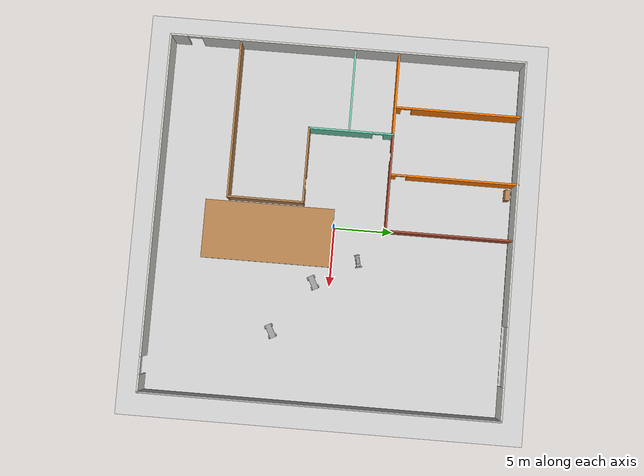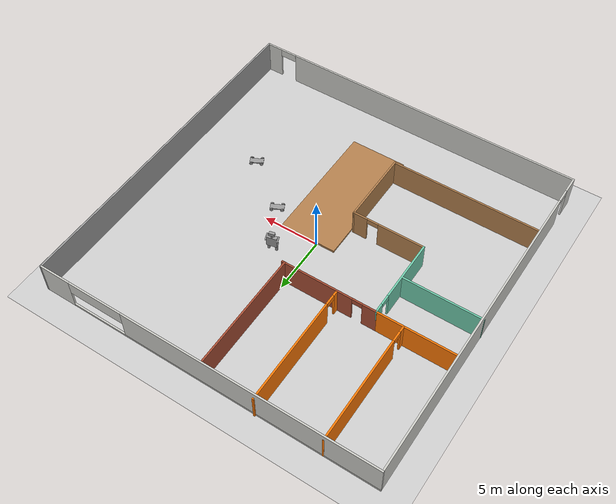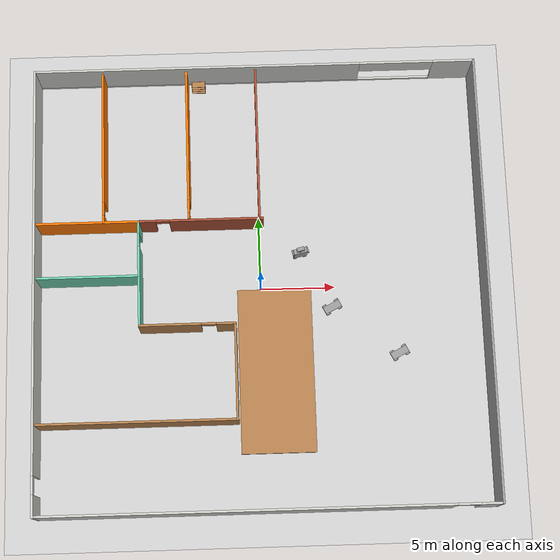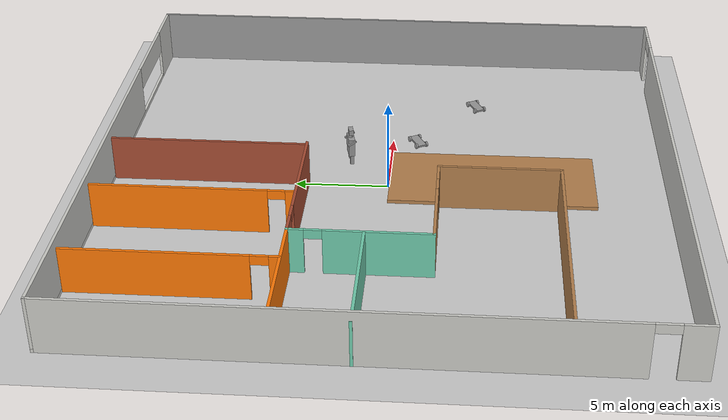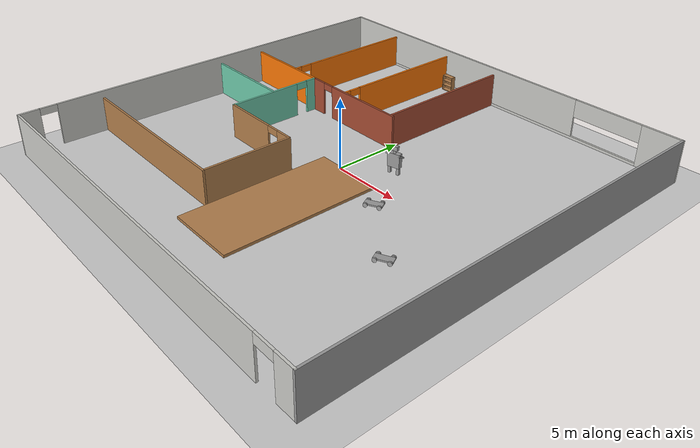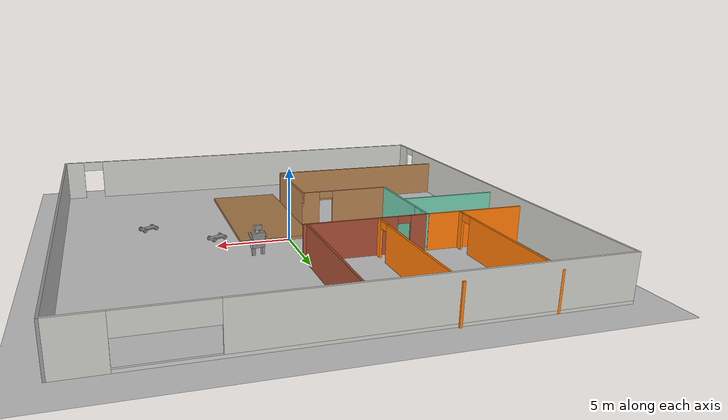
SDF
<sdf version="1.7">
 <world name="default">
  <plugin name="hello" filename="libhello.so"/>
  <light name="sun" type="directional">
   <pose>0 0 10 0 -0 0</pose>
   <diffuse>0.8 0.8 0.8 1</diffuse>
   <specular>0.2 0.2 0.2 1</specular>
   <attenuation>
    <range>1000</range>
    <constant>0.9</constant>
    <linear>0.01</linear>
    <quadratic>0.001</quadratic>
   </attenuation>
   <direction>-0.5 0.1 -0.9</direction>
   <spot><inner_angle>0</inner_angle><outer_angle>0</outer_angle><falloff>0</falloff></spot>
  </light>
  <model name="ground_plane">
   <static>1</static>
   <link name="link">
    <collision name="collision">
     <geometry><plane><normal>0 0 1</normal><size>100 100</size></plane></geometry>
     <surface>
      <contact><collide_bitmask>65535</collide_bitmask></contact>
      <friction><ode><mu>100</mu><mu2>50</mu2></ode></friction>
     </surface>
    </collision>
    <visual name="visual">
     <cast_shadows>0</cast_shadows>
     <geometry><plane><normal>0 0 1</normal><size>100 100</size></plane></geometry>
     <material>
      <script><uri>file://media/materials/scripts/gazebo.material</uri><name>Gazebo/Grey</name></script>
     </material>
    </visual>
   </link>
  </model>
  <gravity>0 0 -9.8</gravity>
  <magnetic_field>6e-06 2.3e-05 -4.2e-05</magnetic_field>
  <atmosphere type="adiabatic"/>
  <physics type="ode">
   <max_step_size>0.001</max_step_size>
   <real_time_factor>1</real_time_factor>
   <real_time_update_rate>1000</real_time_update_rate>
  </physics>
  <scene><ambient>0.4 0.4 0.4 1</ambient><background>0.7 0.7 0.7 1</background><shadows>1</shadows></scene>
  <spherical_coordinates>
   <surface_model>EARTH_WGS84</surface_model>
   <latitude_deg>0</latitude_deg>
   <longitude_deg>0</longitude_deg>
   <elevation>0</elevation>
   <heading_deg>0</heading_deg>
  </spherical_coordinates>
  <model name="7F-2">
   <pose>-0.013384 0.0558 0 0 -0 0</pose>
   <link name="Wall_0">
    <pose>0.013384 -15.0558 0 0 -0 0</pose>
    <visual name="Wall_0_Visual_0">
     <pose>-1.49327 0 1.5 0 -0 0</pose>
     <geometry><box><size>27.1635 0.15 3</size></box></geometry>
     <material>
      <script><uri>file://media/materials/scripts/gazebo.material</uri><name>Gazebo/CeilingTiled</name></script>
      <ambient>1 1 1 1</ambient>
     </material>
     <meta><layer>0</layer></meta>
    </visual>
    <collision name="Wall_0_Collision_0">
     <geometry><box><size>27.1635 0.15 3</size></box></geometry>
     <pose>-1.49327 0 1.5 0 -0 0</pose>
    </collision>
    <visual name="Wall_0_Visual_1">
     <pose>14.3317 0 1.5 0 -0 0</pose>
     <geometry><box><size>1.48654 0.15 3</size></box></geometry>
     <material>
      <script><uri>file://media/materials/scripts/gazebo.material</uri><name>Gazebo/CeilingTiled</name></script>
      <ambient>1 1 1 1</ambient>
     </material>
     <meta><layer>0</layer></meta>
    </visual>
    <collision name="Wall_0_Collision_1">
     <geometry><box><size>1.48654 0.15 3</size></box></geometry>
     <pose>14.3317 0 1.5 0 -0 0</pose>
    </collision>
    <visual name="Wall_0_Visual_2">
     <pose>12.8385 0 2.65 0 -0 0</pose>
     <geometry><box><size>1.5 0.15 0.7</size></box></geometry>
     <material>
      <script><uri>file://media/materials/scripts/gazebo.material</uri><name>Gazebo/CeilingTiled</name></script>
      <ambient>1 1 1 1</ambient>
     </material>
     <meta><layer>0</layer></meta>
    </visual>
    <collision name="Wall_0_Collision_2">
     <geometry><box><size>1.5 0.15 0.7</size></box></geometry>
     <pose>12.8385 0 2.65 0 -0 0</pose>
    </collision>
   </link>
   <link name="Wall_11">
    <pose>-4.68425 9.7558 0 0 -0 -1.5708</pose>
    <visual name="Wall_11_Visual_0">
     <pose>-0.674266 0 1.25 0 -0 0</pose>
     <geometry><box><size>9.40147 0.15 2.5</size></box></geometry>
     <material>
      <script><uri>file://media/materials/scripts/gazebo.material</uri><name>Gazebo/Grey</name></script>
      <ambient>0.996078 0.47451 0.0196078 1</ambient>
     </material>
     <meta><layer>0</layer></meta>
    </visual>
    <collision name="Wall_11_Collision_0">
     <geometry><box><size>9.40147 0.15 2.5</size></box></geometry>
     <pose>-0.674266 0 1.25 0 -0 0</pose>
    </collision>
    <visual name="Wall_11_Visual_1">
     <pose>5.15073 0 1.25 0 -0 0</pose>
     <geometry><box><size>0.448532 0.15 2.5</size></box></geometry>
     <material>
      <script><uri>file://media/materials/scripts/gazebo.material</uri><name>Gazebo/Grey</name></script>
      <ambient>0.996078 0.47451 0.0196078 1</ambient>
     </material>
     <meta><layer>0</layer></meta>
    </visual>
    <collision name="Wall_11_Collision_1">
     <geometry><box><size>0.448532 0.15 2.5</size></box></geometry>
     <pose>5.15073 0 1.25 0 -0 0</pose>
    </collision>
    <visual name="Wall_11_Visual_2">
     <pose>4.47647 0 2.25 0 -0 0</pose>
     <geometry><box><size>0.9 0.15 0.5</size></box></geometry>
     <material>
      <script><uri>file://media/materials/scripts/gazebo.material</uri><name>Gazebo/Grey</name></script>
      <ambient>0.996078 0.47451 0.0196078 1</ambient>
     </material>
     <meta><layer>0</layer></meta>
    </visual>
    <collision name="Wall_11_Collision_2">
     <geometry><box><size>0.9 0.15 0.5</size></box></geometry>
     <pose>4.47647 0 2.25 0 -0 0</pose>
    </collision>
   </link>
   <link name="Wall_13">
    <pose>-10.409 9.6488 0 0 -0 -1.5708</pose>
    <visual name="Wall_13_Visual_0">
     <pose>-0.727769 0 1.25 0 -0 0</pose>
     <geometry><box><size>9.29446 0.15 2.5</size></box></geometry>
     <material>
      <script><uri>file://media/materials/scripts/gazebo.material</uri><name>Gazebo/Grey</name></script>
      <ambient>0.996078 0.47451 0.0196078 1</ambient>
     </material>
     <meta><layer>0</layer></meta>
    </visual>
    <collision name="Wall_13_Collision_0">
     <geometry><box><size>9.29446 0.15 2.5</size></box></geometry>
     <pose>-0.727769 0 1.25 0 -0 0</pose>
    </collision>
    <visual name="Wall_13_Visual_1">
     <pose>5.09723 0 1.25 0 -0 0</pose>
     <geometry><box><size>0.555538 0.15 2.5</size></box></geometry>
     <material>
      <script><uri>file://media/materials/scripts/gazebo.material</uri><name>Gazebo/Grey</name></script>
      <ambient>0.996078 0.47451 0.0196078 1</ambient>
     </material>
     <meta><layer>0</layer></meta>
    </visual>
    <collision name="Wall_13_Collision_1">
     <geometry><box><size>0.555538 0.15 2.5</size></box></geometry>
     <pose>5.09723 0 1.25 0 -0 0</pose>
    </collision>
    <visual name="Wall_13_Visual_2">
     <pose>4.36946 0 2.25 0 -0 0</pose>
     <geometry><box><size>0.9 0.15 0.5</size></box></geometry>
     <material>
      <script><uri>file://media/materials/scripts/gazebo.material</uri><name>Gazebo/Grey</name></script>
      <ambient>0.996078 0.47451 0.0196078 1</ambient>
     </material>
     <meta><layer>0</layer></meta>
    </visual>
    <collision name="Wall_13_Collision_2">
     <geometry><box><size>0.9 0.15 0.5</size></box></geometry>
     <pose>4.36946 0 2.25 0 -0 0</pose>
    </collision>
   </link>
   <link name="Wall_15">
    <pose>-8.07841 0.751801 0 0 -0 -1.5708</pose>
    <visual name="Wall_15_Visual_0">
     <pose>-3.18481 0 1.25 0 -0 0</pose>
     <geometry><box><size>0.880378 0.15 2.5</size></box></geometry>
     <material>
      <script><uri>file://media/materials/scripts/gazebo.material</uri><name>Gazebo/Grey</name></script>
      <ambient>0.435294 0.796078 0.67451 1</ambient>
     </material>
     <meta><layer>0</layer></meta>
    </visual>
    <collision name="Wall_15_Collision_0">
     <geometry><box><size>0.880378 0.15 2.5</size></box></geometry>
     <pose>-3.18481 0 1.25 0 -0 0</pose>
    </collision>
    <visual name="Wall_15_Visual_1">
     <pose>0.890189 0 1.25 0 -0 0</pose>
     <geometry><box><size>5.46962 0.15 2.5</size></box></geometry>
     <material>
      <script><uri>file://media/materials/scripts/gazebo.material</uri><name>Gazebo/Grey</name></script>
      <ambient>0.435294 0.796078 0.67451 1</ambient>
     </material>
     <meta><layer>0</layer></meta>
    </visual>
    <collision name="Wall_15_Collision_1">
     <geometry><box><size>5.46962 0.15 2.5</size></box></geometry>
     <pose>0.890189 0 1.25 0 -0 0</pose>
    </collision>
    <visual name="Wall_15_Visual_2">
     <pose>-2.29462 0 2.25 0 -0 0</pose>
     <geometry><box><size>0.9 0.15 0.5</size></box></geometry>
     <material>
      <script><uri>file://media/materials/scripts/gazebo.material</uri><name>Gazebo/Grey</name></script>
      <ambient>0.435294 0.796078 0.67451 1</ambient>
     </material>
     <meta><layer>0</layer></meta>
    </visual>
    <collision name="Wall_15_Collision_2">
     <geometry><box><size>0.9 0.15 0.5</size></box></geometry>
     <pose>-2.29462 0 2.25 0 -0 0</pose>
    </collision>
   </link>
   <link name="Wall_18">
    <pose>-4.91841 -2.7982 0 0 -0 0</pose>
    <visual name="Wall_18_Visual_0">
     <pose>-1.15754 0 1.25 0 -0 0</pose>
     <geometry><box><size>4.15493 0.15 2.5</size></box></geometry>
     <material>
      <script><uri>file://media/materials/scripts/gazebo.material</uri><name>Gazebo/Wood</name></script>
      <ambient>0.435294 0.796078 0.67451 1</ambient>
     </material>
     <meta><layer>0</layer></meta>
    </visual>
    <collision name="Wall_18_Collision_0">
     <geometry><box><size>4.15493 0.15 2.5</size></box></geometry>
     <pose>-1.15754 0 1.25 0 -0 0</pose>
    </collision>
    <visual name="Wall_18_Visual_1">
     <pose>2.57746 0 1.25 0 -0 0</pose>
     <geometry><box><size>1.31507 0.15 2.5</size></box></geometry>
     <material>
      <script><uri>file://media/materials/scripts/gazebo.material</uri><name>Gazebo/Wood</name></script>
      <ambient>0.435294 0.796078 0.67451 1</ambient>
     </material>
     <meta><layer>0</layer></meta>
    </visual>
    <collision name="Wall_18_Collision_1">
     <geometry><box><size>1.31507 0.15 2.5</size></box></geometry>
     <pose>2.57746 0 1.25 0 -0 0</pose>
    </collision>
    <visual name="Wall_18_Visual_2">
     <pose>1.41993 0 2.25 0 -0 0</pose>
     <geometry><box><size>1 0.15 0.5</size></box></geometry>
     <material>
      <script><uri>file://media/materials/scripts/gazebo.material</uri><name>Gazebo/Wood</name></script>
      <ambient>0.435294 0.796078 0.67451 1</ambient>
     </material>
     <meta><layer>0</layer></meta>
    </visual>
    <collision name="Wall_18_Collision_2">
     <geometry><box><size>1 0.15 0.5</size></box></geometry>
     <pose>1.41993 0 2.25 0 -0 0</pose>
    </collision>
   </link>
   <link name="Wall_19">
    <collision name="Wall_19_Collision">
     <geometry><box><size>6.5 0.15 2.5</size></box></geometry>
     <pose>0 0 1.25 0 -0 0</pose>
    </collision>
    <visual name="Wall_19_Visual">
     <pose>0 0 1.25 0 -0 0</pose>
     <geometry><box><size>6.5 0.15 2.5</size></box></geometry>
     <material>
      <script><uri>file://media/materials/scripts/gazebo.material</uri><name>Gazebo/Wood</name></script>
      <ambient>0.203922 0.396078 0.643137 1</ambient>
     </material>
     <meta><layer>0</layer></meta>
    </visual>
    <pose>-1.75841 -5.9732 0 0 -0 -1.5708</pose>
   </link>
   <link name="Wall_2">
    <collision name="Wall_2_Collision">
     <geometry><box><size>30.15 0.15 3</size></box></geometry>
     <pose>0 0 1.5 0 -0 0</pose>
    </collision>
    <visual name="Wall_2_Visual">
     <pose>0 0 1.5 0 -0 0</pose>
     <geometry><box><size>30.15 0.15 3</size></box></geometry>
     <material>
      <script><uri>file://media/materials/scripts/gazebo.material</uri><name>Gazebo/Grey</name></script>
      <ambient>1 1 1 1</ambient>
     </material>
     <meta><layer>0</layer></meta>
    </visual>
    <pose>15.0134 -0.055802 0 0 -0 1.5708</pose>
   </link>
   <link name="Wall_20">
    <collision name="Wall_20_Collision">
     <geometry><box><size>13.25 0.15 2.5</size></box></geometry>
     <pose>0 0 1.25 0 -0 0</pose>
    </collision>
    <visual name="Wall_20_Visual">
     <pose>0 0 1.25 0 -0 0</pose>
     <geometry><box><size>13.25 0.15 2.5</size></box></geometry>
     <material>
      <script><uri>file://media/materials/scripts/gazebo.material</uri><name>Gazebo/Wood</name></script>
      <ambient>0.203922 0.396078 0.643137 1</ambient>
     </material>
     <meta><layer>0</layer></meta>
    </visual>
    <pose>-8.30841 -9.1482 0 0 -0 3.14159</pose>
   </link>
   <link name="Wall_24">
    <collision name="Wall_24_Collision">
     <geometry><box><size>7.03 0.15 2.5</size></box></geometry>
     <pose>0 0 1.25 0 -0 0</pose>
    </collision>
    <visual name="Wall_24_Visual">
     <pose>0 0 1.25 0 -0 0</pose>
     <geometry><box><size>7.03 0.15 2.5</size></box></geometry>
     <material>
      <script><uri>file://media/materials/scripts/gazebo.material</uri><name>Gazebo/Grey</name></script>
      <ambient>0.996078 0.47451 0.0196078 1</ambient>
     </material>
     <meta><layer>0</layer></meta>
    </visual>
    <pose>-11.5184 4.3018 0 0 -0 3.14159</pose>
   </link>
   <link name="Wall_26">
    <pose>-3.91341 4.3018 0 0 -0 0</pose>
    <visual name="Wall_26_Visual_0">
     <pose>-3.62084 0 1.25 0 -0 0</pose>
     <geometry><box><size>1.25833 0.15 2.5</size></box></geometry>
     <material>
      <script><uri>file://media/materials/scripts/gazebo.material</uri><name>Gazebo/Bricks</name></script>
      <ambient>1 1 1 1</ambient>
     </material>
     <meta><layer>0</layer></meta>
    </visual>
    <collision name="Wall_26_Collision_0">
     <geometry><box><size>1.25833 0.15 2.5</size></box></geometry>
     <pose>-3.62084 0 1.25 0 -0 0</pose>
    </collision>
    <visual name="Wall_26_Visual_1">
     <pose>1.07916 0 1.25 0 -0 0</pose>
     <geometry><box><size>6.34167 0.15 2.5</size></box></geometry>
     <material>
      <script><uri>file://media/materials/scripts/gazebo.material</uri><name>Gazebo/Bricks</name></script>
      <ambient>1 1 1 1</ambient>
     </material>
     <meta><layer>0</layer></meta>
    </visual>
    <collision name="Wall_26_Collision_1">
     <geometry><box><size>6.34167 0.15 2.5</size></box></geometry>
     <pose>1.07916 0 1.25 0 -0 0</pose>
    </collision>
    <visual name="Wall_26_Visual_2">
     <pose>-2.54167 0 2.25 0 -0 0</pose>
     <geometry><box><size>0.9 0.15 0.5</size></box></geometry>
     <material>
      <script><uri>file://media/materials/scripts/gazebo.material</uri><name>Gazebo/Bricks</name></script>
      <ambient>1 1 1 1</ambient>
     </material>
     <meta><layer>0</layer></meta>
    </visual>
    <collision name="Wall_26_Collision_2">
     <geometry><box><size>0.9 0.15 0.5</size></box></geometry>
     <pose>-2.54167 0 2.25 0 -0 0</pose>
    </collision>
   </link>
   <link name="Wall_30">
    <collision name="Wall_30_Collision">
     <geometry><box><size>7 0.15 2.5</size></box></geometry>
     <pose>0 0 1.25 0 -0 0</pose>
    </collision>
    <visual name="Wall_30_Visual">
     <pose>0 0 1.25 0 -0 0</pose>
     <geometry><box><size>7 0.15 2.5</size></box></geometry>
     <material>
      <script><uri>file://media/materials/scripts/gazebo.material</uri><name>Gazebo/Grey</name></script>
      <ambient>0.435294 0.796078 0.67451 1</ambient>
     </material>
     <meta><layer>0</layer></meta>
    </visual>
    <pose>-11.5884 0.576344 0 0 -0 0</pose>
   </link>
   <link name="Wall_35">
    <collision name="Wall_35_Collision">
     <geometry><box><size>11.1 5 0.2</size></box></geometry>
     <pose>0 0 0.1 0 -0 0</pose>
    </collision>
    <visual name="Wall_35_Visual">
     <pose>0 0 0.1 0 -0 0</pose>
     <geometry><box><size>11.1 5 0.2</size></box></geometry>
     <material>
      <script><uri>file://media/materials/scripts/gazebo.material</uri><name>Gazebo/Wood</name></script>
      <ambient>1 1 1 1</ambient>
     </material>
     <meta><layer>0</layer></meta>
    </visual>
    <pose>0.909882 -5.6625 0 0 -0 -1.5708</pose>
   </link>
   <link name="Wall_4">
    <pose>0.013384 14.9442 0 0 -0 3.14159</pose>
    <visual name="Wall_4_Visual_0">
     <pose>-13.6482 0 1.5 0 -0 0</pose>
     <geometry><box><size>2.85357 0.15 3</size></box></geometry>
     <material>
      <script><uri>file://media/materials/scripts/gazebo.material</uri><name>Gazebo/CeilingTiled</name></script>
      <ambient>1 1 1 1</ambient>
     </material>
     <meta><layer>0</layer></meta>
    </visual>
    <collision name="Wall_4_Collision_0">
     <geometry><box><size>2.85357 0.15 3</size></box></geometry>
     <pose>-13.6482 0 1.5 0 -0 0</pose>
    </collision>
    <visual name="Wall_4_Visual_1">
     <pose>1.42679 0 0.1 0 -0 0</pose>
     <geometry><box><size>27.2964 0.15 0.2</size></box></geometry>
     <material>
      <script><uri>file://media/materials/scripts/gazebo.material</uri><name>Gazebo/CeilingTiled</name></script>
      <ambient>1 1 1 1</ambient>
     </material>
     <meta><layer>0</layer></meta>
    </visual>
    <collision name="Wall_4_Collision_1">
     <geometry><box><size>27.2964 0.15 0.2</size></box></geometry>
     <pose>1.42679 0 0.1 0 -0 0</pose>
    </collision>
    <visual name="Wall_4_Visual_2">
     <pose>3.92679 0 1.6 0 -0 0</pose>
     <geometry><box><size>22.2964 0.15 2.8</size></box></geometry>
     <material>
      <script><uri>file://media/materials/scripts/gazebo.material</uri><name>Gazebo/CeilingTiled</name></script>
      <ambient>1 1 1 1</ambient>
     </material>
     <meta><layer>0</layer></meta>
    </visual>
    <collision name="Wall_4_Collision_2">
     <geometry><box><size>22.2964 0.15 2.8</size></box></geometry>
     <pose>3.92679 0 1.6 0 -0 0</pose>
    </collision>
    <visual name="Wall_4_Visual_3">
     <pose>-9.72143 0 2.35 0 -0 0</pose>
     <geometry><box><size>5 0.15 1.3</size></box></geometry>
     <material>
      <script><uri>file://media/materials/scripts/gazebo.material</uri><name>Gazebo/CeilingTiled</name></script>
      <ambient>1 1 1 1</ambient>
     </material>
     <meta><layer>0</layer></meta>
    </visual>
    <collision name="Wall_4_Collision_3">
     <geometry><box><size>5 0.15 1.3</size></box></geometry>
     <pose>-9.72143 0 2.35 0 -0 0</pose>
    </collision>
   </link>
   <link name="Wall_6">
    <pose>-14.9866 -0.055802 0 0 -0 -1.5708</pose>
    <visual name="Wall_6_Visual_0">
     <pose>-1.34384 0 1.5 0 -0 0</pose>
     <geometry><box><size>27.4623 0.15 3</size></box></geometry>
     <material>
      <script><uri>file://media/materials/scripts/gazebo.material</uri><name>Gazebo/CeilingTiled</name></script>
      <ambient>1 1 1 1</ambient>
     </material>
     <meta><layer>0</layer></meta>
    </visual>
    <collision name="Wall_6_Collision_0">
     <geometry><box><size>27.4623 0.15 3</size></box></geometry>
     <pose>-1.34384 0 1.5 0 -0 0</pose>
    </collision>
    <visual name="Wall_6_Visual_1">
     <pose>14.3312 0 1.5 0 -0 0</pose>
     <geometry><box><size>1.48768 0.15 3</size></box></geometry>
     <material>
      <script><uri>file://media/materials/scripts/gazebo.material</uri><name>Gazebo/CeilingTiled</name></script>
      <ambient>1 1 1 1</ambient>
     </material>
     <meta><layer>0</layer></meta>
    </visual>
    <collision name="Wall_6_Collision_1">
     <geometry><box><size>1.48768 0.15 3</size></box></geometry>
     <pose>14.3312 0 1.5 0 -0 0</pose>
    </collision>
    <visual name="Wall_6_Visual_2">
     <pose>12.9873 0 2.75 0 -0 0</pose>
     <geometry><box><size>1.2 0.15 0.5</size></box></geometry>
     <material>
      <script><uri>file://media/materials/scripts/gazebo.material</uri><name>Gazebo/CeilingTiled</name></script>
      <ambient>1 1 1 1</ambient>
     </material>
     <meta><layer>0</layer></meta>
    </visual>
    <collision name="Wall_6_Collision_2">
     <geometry><box><size>1.2 0.15 0.5</size></box></geometry>
     <pose>12.9873 0 2.75 0 -0 0</pose>
    </collision>
   </link>
   <link name="Wall_8">
    <collision name="Wall_8_Collision">
     <geometry><box><size>10.75 0.15 2.5</size></box></geometry>
     <pose>0 0 1.25 0 -0 0</pose>
    </collision>
    <visual name="Wall_8_Visual">
     <pose>0 0 1.25 0 -0 0</pose>
     <geometry><box><size>10.75 0.15 2.5</size></box></geometry>
     <material>
      <script><uri>file://media/materials/scripts/gazebo.material</uri><name>Gazebo/Bricks</name></script>
      <ambient>1 1 1 1</ambient>
     </material>
     <meta><layer>0</layer></meta>
    </visual>
    <pose>0.064743 9.61919 0 0 -0 -1.5708</pose>
   </link>
   <static>1</static>
  </model>
  <model name="little_car">
   <link name="link_1">
    <inertial>
     <mass>1</mass>
     <inertia>
      <ixx>0.166667</ixx>
      <ixy>0</ixy>
      <ixz>0</ixz>
      <iyy>0.166667</iyy>
      <iyz>0</iyz>
      <izz>0.166667</izz>
     </inertia>
    </inertial>
    <pose>-0.316357 -0.367633 0 0 -0 0</pose>
    <visual name="visual">
     <geometry><box><size>1.2 0.5 0.1</size></box></geometry>
     <material>
      <lighting>1</lighting>
      <script><uri>file://media/materials/scripts/gazebo.material</uri><name>Gazebo/Grey</name></script>
      <shader type="pixel"><normal_map>__default__</normal_map></shader>
      <ambient>0.3 0.3 0.3 1</ambient>
      <diffuse>0.7 0.7 0.7 1</diffuse>
      <specular>0.204 0.396 0.643 1</specular>
      <emissive>0.204 0.396 0.643 1</emissive>
     </material>
    </visual>
    <collision name="collision">
     <geometry><box><size>1.2 0.5 0.1</size></box></geometry>
     <surface>
      <friction>
       <ode><mu>1</mu><mu2>1</mu2><fdir1>0 0 0</fdir1><slip1>0</slip1><slip2>0</slip2></ode>
       <torsional>
        <coefficient>1</coefficient>
        <patch_radius>0</patch_radius>
        <surface_radius>0</surface_radius>
        <use_patch_radius>1</use_patch_radius>
        <ode><slip>0</slip></ode>
       </torsional>
      </friction>
      <bounce><restitution_coefficient>0</restitution_coefficient><threshold>1e+06</threshold></bounce>
      <contact>
       <collide_without_contact>0</collide_without_contact>
       <collide_without_contact_bitmask>1</collide_without_contact_bitmask>
       <collide_bitmask>1</collide_bitmask>
       <ode>
        <soft_cfm>0</soft_cfm>
        <soft_erp>0.2</soft_erp>
        <kp>1e+13</kp>
        <kd>1</kd>
        <max_vel>0.01</max_vel>
        <min_depth>0</min_depth>
       </ode>
       <bullet>
        <split_impulse>1</split_impulse>
        <split_impulse_penetration_threshold>-0.01</split_impulse_penetration_threshold>
        <soft_cfm>0</soft_cfm>
        <soft_erp>0.2</soft_erp>
        <kp>1e+13</kp>
        <kd>1</kd>
       </bullet>
      </contact>
     </surface>
    </collision>
   </link>
   <link name="link_2">
    <inertial>
     <mass>1</mass>
     <inertia><ixx>0.145833</ixx><ixy>0</ixy><ixz>0</ixz><iyy>0.145833</iyy><iyz>0</iyz><izz>0.125</izz></inertia>
    </inertial>
    <pose>-0.766357 -0.667648 -0.015 1.5707 -0 0</pose>
    <visual name="visual">
     <geometry><cylinder><radius>0.15</radius><length>0.1</length></cylinder></geometry>
     <material>
      <lighting>1</lighting>
      <script><uri>file://media/materials/scripts/gazebo.material</uri><name>Gazebo/Grey</name></script>
      <shader type="pixel"><normal_map>__default__</normal_map></shader>
      <ambient>0.3 0.3 0.3 1</ambient>
      <diffuse>0.7 0.7 0.7 1</diffuse>
      <specular>0.204 0.396 0.643 1</specular>
      <emissive>0.961 0.475 0 1</emissive>
     </material>
    </visual>
    <collision name="collision">
     <geometry><cylinder><radius>0.15</radius><length>0.1</length></cylinder></geometry>
     <surface>
      <friction>
       <ode><mu>1</mu><mu2>1</mu2><fdir1>0 0 0</fdir1><slip1>0</slip1><slip2>0</slip2></ode>
       <torsional>
        <coefficient>1</coefficient>
        <patch_radius>0</patch_radius>
        <surface_radius>0</surface_radius>
        <use_patch_radius>1</use_patch_radius>
        <ode><slip>0</slip></ode>
       </torsional>
      </friction>
      <bounce><restitution_coefficient>0</restitution_coefficient><threshold>1e+06</threshold></bounce>
      <contact>
       <collide_without_contact>0</collide_without_contact>
       <collide_without_contact_bitmask>1</collide_without_contact_bitmask>
       <collide_bitmask>1</collide_bitmask>
       <ode>
        <soft_cfm>0</soft_cfm>
        <soft_erp>0.2</soft_erp>
        <kp>1e+13</kp>
        <kd>1</kd>
        <max_vel>0.01</max_vel>
        <min_depth>0</min_depth>
       </ode>
       <bullet>
        <split_impulse>1</split_impulse>
        <split_impulse_penetration_threshold>-0.01</split_impulse_penetration_threshold>
        <soft_cfm>0</soft_cfm>
        <soft_erp>0.2</soft_erp>
        <kp>1e+13</kp>
        <kd>1</kd>
       </bullet>
      </contact>
     </surface>
    </collision>
   </link>
   <link name="link_2_clone">
    <inertial>
     <mass>1</mass>
     <inertia><ixx>0.145833</ixx><ixy>0</ixy><ixz>0</ixz><iyy>0.145833</iyy><iyz>0</iyz><izz>0.125</izz></inertia>
    </inertial>
    <pose>0.133643 -0.667648 -0.015 1.5707 -0 0</pose>
    <visual name="visual">
     <geometry><cylinder><radius>0.15</radius><length>0.1</length></cylinder></geometry>
     <material>
      <lighting>1</lighting>
      <script><uri>file://media/materials/scripts/gazebo.material</uri><name>Gazebo/Grey</name></script>
      <shader type="pixel"><normal_map>__default__</normal_map></shader>
      <ambient>0.3 0.3 0.3 1</ambient>
      <diffuse>0.7 0.7 0.7 1</diffuse>
      <specular>0.204 0.396 0.643 1</specular>
      <emissive>0.961 0.475 0 1</emissive>
     </material>
    </visual>
    <collision name="collision">
     <geometry><cylinder><radius>0.15</radius><length>0.1</length></cylinder></geometry>
     <surface>
      <friction>
       <ode><mu>1</mu><mu2>1</mu2><fdir1>0 0 0</fdir1><slip1>0</slip1><slip2>0</slip2></ode>
       <torsional>
        <coefficient>1</coefficient>
        <patch_radius>0</patch_radius>
        <surface_radius>0</surface_radius>
        <use_patch_radius>1</use_patch_radius>
        <ode><slip>0</slip></ode>
       </torsional>
      </friction>
      <bounce><restitution_coefficient>0</restitution_coefficient><threshold>1e+06</threshold></bounce>
      <contact>
       <collide_without_contact>0</collide_without_contact>
       <collide_without_contact_bitmask>1</collide_without_contact_bitmask>
       <collide_bitmask>1</collide_bitmask>
       <ode>
        <soft_cfm>0</soft_cfm>
        <soft_erp>0.2</soft_erp>
        <kp>1e+13</kp>
        <kd>1</kd>
        <max_vel>0.01</max_vel>
        <min_depth>0</min_depth>
       </ode>
       <bullet>
        <split_impulse>1</split_impulse>
        <split_impulse_penetration_threshold>-0.01</split_impulse_penetration_threshold>
        <soft_cfm>0</soft_cfm>
        <soft_erp>0.2</soft_erp>
        <kp>1e+13</kp>
        <kd>1</kd>
       </bullet>
      </contact>
     </surface>
    </collision>
   </link>
   <link name="link_2_clone_0">
    <inertial>
     <mass>1</mass>
     <inertia><ixx>0.145833</ixx><ixy>0</ixy><ixz>0</ixz><iyy>0.145833</iyy><iyz>0</iyz><izz>0.125</izz></inertia>
    </inertial>
    <pose>-0.766357 -0.067619 -0.015 1.5707 -0 0</pose>
    <visual name="visual">
     <geometry><cylinder><radius>0.15</radius><length>0.1</length></cylinder></geometry>
     <material>
      <lighting>1</lighting>
      <script><uri>file://media/materials/scripts/gazebo.material</uri><name>Gazebo/Grey</name></script>
      <shader type="pixel"><normal_map>__default__</normal_map></shader>
      <ambient>0.3 0.3 0.3 1</ambient>
      <diffuse>0.7 0.7 0.7 1</diffuse>
      <specular>0.204 0.396 0.643 1</specular>
      <emissive>0.961 0.475 0 1</emissive>
     </material>
    </visual>
    <collision name="collision">
     <geometry><cylinder><radius>0.15</radius><length>0.1</length></cylinder></geometry>
     <surface>
      <friction>
       <ode><mu>1</mu><mu2>1</mu2><fdir1>0 0 0</fdir1><slip1>0</slip1><slip2>0</slip2></ode>
       <torsional>
        <coefficient>1</coefficient>
        <patch_radius>0</patch_radius>
        <surface_radius>0</surface_radius>
        <use_patch_radius>1</use_patch_radius>
        <ode><slip>0</slip></ode>
       </torsional>
      </friction>
      <bounce><restitution_coefficient>0</restitution_coefficient><threshold>1e+06</threshold></bounce>
      <contact>
       <collide_without_contact>0</collide_without_contact>
       <collide_without_contact_bitmask>1</collide_without_contact_bitmask>
       <collide_bitmask>1</collide_bitmask>
       <ode>
        <soft_cfm>0</soft_cfm>
        <soft_erp>0.2</soft_erp>
        <kp>1e+13</kp>
        <kd>1</kd>
        <max_vel>0.01</max_vel>
        <min_depth>0</min_depth>
       </ode>
       <bullet>
        <split_impulse>1</split_impulse>
        <split_impulse_penetration_threshold>-0.01</split_impulse_penetration_threshold>
        <soft_cfm>0</soft_cfm>
        <soft_erp>0.2</soft_erp>
        <kp>1e+13</kp>
        <kd>1</kd>
       </bullet>
      </contact>
     </surface>
    </collision>
   </link>
   <link name="link_2_clone_1">
    <inertial>
     <mass>1</mass>
     <inertia><ixx>0.145833</ixx><ixy>0</ixy><ixz>0</ixz><iyy>0.145833</iyy><iyz>0</iyz><izz>0.125</izz></inertia>
    </inertial>
    <pose>0.133643 -0.067619 -0.015 1.5707 -0 0</pose>
    <visual name="visual">
     <geometry><cylinder><radius>0.15</radius><length>0.1</length></cylinder></geometry>
     <material>
      <lighting>1</lighting>
      <script><uri>file://media/materials/scripts/gazebo.material</uri><name>Gazebo/Grey</name></script>
      <shader type="pixel"><normal_map>__default__</normal_map></shader>
      <ambient>0.3 0.3 0.3 1</ambient>
      <diffuse>0.7 0.7 0.7 1</diffuse>
      <specular>0.204 0.396 0.643 1</specular>
      <emissive>0.961 0.475 0 1</emissive>
     </material>
    </visual>
    <collision name="collision">
     <geometry><cylinder><radius>0.15</radius><length>0.1</length></cylinder></geometry>
     <surface>
      <friction>
       <ode><mu>1</mu><mu2>1</mu2><fdir1>0 0 0</fdir1><slip1>0</slip1><slip2>0</slip2></ode>
       <torsional>
        <coefficient>1</coefficient>
        <patch_radius>0</patch_radius>
        <surface_radius>0</surface_radius>
        <use_patch_radius>1</use_patch_radius>
        <ode><slip>0</slip></ode>
       </torsional>
      </friction>
      <bounce><restitution_coefficient>0</restitution_coefficient><threshold>1e+06</threshold></bounce>
      <contact>
       <collide_without_contact>0</collide_without_contact>
       <collide_without_contact_bitmask>1</collide_without_contact_bitmask>
       <collide_bitmask>1</collide_bitmask>
       <ode>
        <soft_cfm>0</soft_cfm>
        <soft_erp>0.2</soft_erp>
        <kp>1e+13</kp>
        <kd>1</kd>
        <max_vel>0.01</max_vel>
        <min_depth>0</min_depth>
       </ode>
       <bullet>
        <split_impulse>1</split_impulse>
        <split_impulse_penetration_threshold>-0.01</split_impulse_penetration_threshold>
        <soft_cfm>0</soft_cfm>
        <soft_erp>0.2</soft_erp>
        <kp>1e+13</kp>
        <kd>1</kd>
       </bullet>
      </contact>
     </surface>
    </collision>
   </link>
   <joint name="link_1_JOINT_1" type="revolute">
    <parent>link_1</parent>
    <child>link_2</child>
    <axis>
     <xyz>0 0 1</xyz>
     <limit>
      <lower>-1.79769e+308</lower>
      <upper>1.79769e+308</upper>
      <effort>-1</effort>
      <velocity>-1</velocity>
     </limit>
     <dynamics>
      <spring_reference>0</spring_reference>
      <spring_stiffness>0</spring_stiffness>
      <damping>0</damping>
      <friction>0</friction>
     </dynamics>
    </axis>
    <physics>
     <ode><limit><cfm>0</cfm><erp>0.2</erp></limit><suspension><cfm>0</cfm><erp>0.2</erp></suspension></ode>
    </physics>
   </joint>
   <joint name="link_1_JOINT_2" type="revolute">
    <parent>link_1</parent>
    <child>link_2_clone_0</child>
    <axis>
     <xyz>0 0 1</xyz>
     <limit>
      <lower>-1.79769e+308</lower>
      <upper>1.79769e+308</upper>
      <effort>-1</effort>
      <velocity>-1</velocity>
     </limit>
     <dynamics>
      <spring_reference>0</spring_reference>
      <spring_stiffness>0</spring_stiffness>
      <damping>0</damping>
      <friction>0</friction>
     </dynamics>
    </axis>
    <physics>
     <ode><limit><cfm>0</cfm><erp>0.2</erp></limit><suspension><cfm>0</cfm><erp>0.2</erp></suspension></ode>
    </physics>
   </joint>
   <joint name="link_1_JOINT_3" type="revolute">
    <parent>link_1</parent>
    <child>link_2_clone</child>
    <axis>
     <xyz>0 0 1</xyz>
     <limit>
      <lower>-1.79769e+308</lower>
      <upper>1.79769e+308</upper>
      <effort>-1</effort>
      <velocity>-1</velocity>
     </limit>
     <dynamics>
      <spring_reference>0</spring_reference>
      <spring_stiffness>0</spring_stiffness>
      <damping>0</damping>
      <friction>0</friction>
     </dynamics>
    </axis>
    <physics>
     <ode><limit><cfm>0</cfm><erp>0.2</erp></limit><suspension><cfm>0</cfm><erp>0.2</erp></suspension></ode>
    </physics>
   </joint>
   <joint name="link_1_JOINT_4" type="revolute">
    <parent>link_1</parent>
    <child>link_2_clone_1</child>
    <axis>
     <xyz>1 0 0</xyz>
     <limit>
      <lower>-1.79769e+308</lower>
      <upper>1.79769e+308</upper>
      <effort>-1</effort>
      <velocity>-1</velocity>
     </limit>
     <dynamics>
      <spring_reference>0</spring_reference>
      <spring_stiffness>0</spring_stiffness>
      <damping>0</damping>
      <friction>0</friction>
     </dynamics>
    </axis>
    <physics>
     <ode><limit><cfm>0</cfm><erp>0.2</erp></limit><suspension><cfm>0</cfm><erp>0.2</erp></suspension></ode>
    </physics>
   </joint>
   <static>0</static>
   <pose>4.91111 -0.915481 0.164993 -5e-06 1.5e-05 0.473483</pose>
  </model>
  <model name="little_car_0">
   <link name="link_1">
    <inertial>
     <mass>1</mass>
     <inertia>
      <ixx>0.166667</ixx>
      <ixy>0</ixy>
      <ixz>0</ixz>
      <iyy>0.166667</iyy>
      <iyz>0</iyz>
      <izz>0.166667</izz>
     </inertia>
    </inertial>
    <pose>-0.316357 -0.367633 0 0 -0 0</pose>
    <visual name="visual">
     <geometry><box><size>1.2 0.5 0.1</size></box></geometry>
     <material>
      <lighting>1</lighting>
      <script><uri>file://media/materials/scripts/gazebo.material</uri><name>Gazebo/Grey</name></script>
      <shader type="pixel"><normal_map>__default__</normal_map></shader>
      <ambient>0.3 0.3 0.3 1</ambient>
      <diffuse>0.7 0.7 0.7 1</diffuse>
      <specular>0.204 0.396 0.643 1</specular>
      <emissive>0.204 0.396 0.643 1</emissive>
     </material>
    </visual>
    <collision name="collision">
     <geometry><box><size>1.2 0.5 0.1</size></box></geometry>
     <surface>
      <friction>
       <ode><mu>1</mu><mu2>1</mu2><fdir1>0 0 0</fdir1><slip1>0</slip1><slip2>0</slip2></ode>
       <torsional>
        <coefficient>1</coefficient>
        <patch_radius>0</patch_radius>
        <surface_radius>0</surface_radius>
        <use_patch_radius>1</use_patch_radius>
        <ode><slip>0</slip></ode>
       </torsional>
      </friction>
      <bounce><restitution_coefficient>0</restitution_coefficient><threshold>1e+06</threshold></bounce>
      <contact>
       <collide_without_contact>0</collide_without_contact>
       <collide_without_contact_bitmask>1</collide_without_contact_bitmask>
       <collide_bitmask>1</collide_bitmask>
       <ode>
        <soft_cfm>0</soft_cfm>
        <soft_erp>0.2</soft_erp>
        <kp>1e+13</kp>
        <kd>1</kd>
        <max_vel>0.01</max_vel>
        <min_depth>0</min_depth>
       </ode>
       <bullet>
        <split_impulse>1</split_impulse>
        <split_impulse_penetration_threshold>-0.01</split_impulse_penetration_threshold>
        <soft_cfm>0</soft_cfm>
        <soft_erp>0.2</soft_erp>
        <kp>1e+13</kp>
        <kd>1</kd>
       </bullet>
      </contact>
     </surface>
    </collision>
   </link>
   <link name="link_2">
    <inertial>
     <mass>1</mass>
     <inertia><ixx>0.145833</ixx><ixy>0</ixy><ixz>0</ixz><iyy>0.145833</iyy><iyz>0</iyz><izz>0.125</izz></inertia>
    </inertial>
    <pose>-0.766357 -0.667648 -0.015 1.5707 -0 0</pose>
    <visual name="visual">
     <geometry><cylinder><radius>0.15</radius><length>0.1</length></cylinder></geometry>
     <material>
      <lighting>1</lighting>
      <script><uri>file://media/materials/scripts/gazebo.material</uri><name>Gazebo/Grey</name></script>
      <shader type="pixel"><normal_map>__default__</normal_map></shader>
      <ambient>0.3 0.3 0.3 1</ambient>
      <diffuse>0.7 0.7 0.7 1</diffuse>
      <specular>0.204 0.396 0.643 1</specular>
      <emissive>0.961 0.475 0 1</emissive>
     </material>
    </visual>
    <collision name="collision">
     <geometry><cylinder><radius>0.15</radius><length>0.1</length></cylinder></geometry>
     <surface>
      <friction>
       <ode><mu>1</mu><mu2>1</mu2><fdir1>0 0 0</fdir1><slip1>0</slip1><slip2>0</slip2></ode>
       <torsional>
        <coefficient>1</coefficient>
        <patch_radius>0</patch_radius>
        <surface_radius>0</surface_radius>
        <use_patch_radius>1</use_patch_radius>
        <ode><slip>0</slip></ode>
       </torsional>
      </friction>
      <bounce><restitution_coefficient>0</restitution_coefficient><threshold>1e+06</threshold></bounce>
      <contact>
       <collide_without_contact>0</collide_without_contact>
       <collide_without_contact_bitmask>1</collide_without_contact_bitmask>
       <collide_bitmask>1</collide_bitmask>
       <ode>
        <soft_cfm>0</soft_cfm>
        <soft_erp>0.2</soft_erp>
        <kp>1e+13</kp>
        <kd>1</kd>
        <max_vel>0.01</max_vel>
        <min_depth>0</min_depth>
       </ode>
       <bullet>
        <split_impulse>1</split_impulse>
        <split_impulse_penetration_threshold>-0.01</split_impulse_penetration_threshold>
        <soft_cfm>0</soft_cfm>
        <soft_erp>0.2</soft_erp>
        <kp>1e+13</kp>
        <kd>1</kd>
       </bullet>
      </contact>
     </surface>
    </collision>
   </link>
   <link name="link_2_clone">
    <inertial>
     <mass>1</mass>
     <inertia><ixx>0.145833</ixx><ixy>0</ixy><ixz>0</ixz><iyy>0.145833</iyy><iyz>0</iyz><izz>0.125</izz></inertia>
    </inertial>
    <pose>0.133643 -0.667648 -0.015 1.5707 -0 0</pose>
    <visual name="visual">
     <geometry><cylinder><radius>0.15</radius><length>0.1</length></cylinder></geometry>
     <material>
      <lighting>1</lighting>
      <script><uri>file://media/materials/scripts/gazebo.material</uri><name>Gazebo/Grey</name></script>
      <shader type="pixel"><normal_map>__default__</normal_map></shader>
      <ambient>0.3 0.3 0.3 1</ambient>
      <diffuse>0.7 0.7 0.7 1</diffuse>
      <specular>0.204 0.396 0.643 1</specular>
      <emissive>0.961 0.475 0 1</emissive>
     </material>
    </visual>
    <collision name="collision">
     <geometry><cylinder><radius>0.15</radius><length>0.1</length></cylinder></geometry>
     <surface>
      <friction>
       <ode><mu>1</mu><mu2>1</mu2><fdir1>0 0 0</fdir1><slip1>0</slip1><slip2>0</slip2></ode>
       <torsional>
        <coefficient>1</coefficient>
        <patch_radius>0</patch_radius>
        <surface_radius>0</surface_radius>
        <use_patch_radius>1</use_patch_radius>
        <ode><slip>0</slip></ode>
       </torsional>
      </friction>
      <bounce><restitution_coefficient>0</restitution_coefficient><threshold>1e+06</threshold></bounce>
      <contact>
       <collide_without_contact>0</collide_without_contact>
       <collide_without_contact_bitmask>1</collide_without_contact_bitmask>
       <collide_bitmask>1</collide_bitmask>
       <ode>
        <soft_cfm>0</soft_cfm>
        <soft_erp>0.2</soft_erp>
        <kp>1e+13</kp>
        <kd>1</kd>
        <max_vel>0.01</max_vel>
        <min_depth>0</min_depth>
       </ode>
       <bullet>
        <split_impulse>1</split_impulse>
        <split_impulse_penetration_threshold>-0.01</split_impulse_penetration_threshold>
        <soft_cfm>0</soft_cfm>
        <soft_erp>0.2</soft_erp>
        <kp>1e+13</kp>
        <kd>1</kd>
       </bullet>
      </contact>
     </surface>
    </collision>
   </link>
   <link name="link_2_clone_0">
    <inertial>
     <mass>1</mass>
     <inertia><ixx>0.145833</ixx><ixy>0</ixy><ixz>0</ixz><iyy>0.145833</iyy><iyz>0</iyz><izz>0.125</izz></inertia>
    </inertial>
    <pose>-0.766357 -0.067619 -0.015 1.5707 -0 0</pose>
    <visual name="visual">
     <geometry><cylinder><radius>0.15</radius><length>0.1</length></cylinder></geometry>
     <material>
      <lighting>1</lighting>
      <script><uri>file://media/materials/scripts/gazebo.material</uri><name>Gazebo/Grey</name></script>
      <shader type="pixel"><normal_map>__default__</normal_map></shader>
      <ambient>0.3 0.3 0.3 1</ambient>
      <diffuse>0.7 0.7 0.7 1</diffuse>
      <specular>0.204 0.396 0.643 1</specular>
      <emissive>0.961 0.475 0 1</emissive>
     </material>
    </visual>
    <collision name="collision">
     <geometry><cylinder><radius>0.15</radius><length>0.1</length></cylinder></geometry>
     <surface>
      <friction>
       <ode><mu>1</mu><mu2>1</mu2><fdir1>0 0 0</fdir1><slip1>0</slip1><slip2>0</slip2></ode>
       <torsional>
        <coefficient>1</coefficient>
        <patch_radius>0</patch_radius>
        <surface_radius>0</surface_radius>
        <use_patch_radius>1</use_patch_radius>
        <ode><slip>0</slip></ode>
       </torsional>
      </friction>
      <bounce><restitution_coefficient>0</restitution_coefficient><threshold>1e+06</threshold></bounce>
      <contact>
       <collide_without_contact>0</collide_without_contact>
       <collide_without_contact_bitmask>1</collide_without_contact_bitmask>
       <collide_bitmask>1</collide_bitmask>
       <ode>
        <soft_cfm>0</soft_cfm>
        <soft_erp>0.2</soft_erp>
        <kp>1e+13</kp>
        <kd>1</kd>
        <max_vel>0.01</max_vel>
        <min_depth>0</min_depth>
       </ode>
       <bullet>
        <split_impulse>1</split_impulse>
        <split_impulse_penetration_threshold>-0.01</split_impulse_penetration_threshold>
        <soft_cfm>0</soft_cfm>
        <soft_erp>0.2</soft_erp>
        <kp>1e+13</kp>
        <kd>1</kd>
       </bullet>
      </contact>
     </surface>
    </collision>
   </link>
   <link name="link_2_clone_1">
    <inertial>
     <mass>1</mass>
     <inertia><ixx>0.145833</ixx><ixy>0</ixy><ixz>0</ixz><iyy>0.145833</iyy><iyz>0</iyz><izz>0.125</izz></inertia>
    </inertial>
    <pose>0.133643 -0.067619 -0.015 1.5707 -0 0</pose>
    <visual name="visual">
     <geometry><cylinder><radius>0.15</radius><length>0.1</length></cylinder></geometry>
     <material>
      <lighting>1</lighting>
      <script><uri>file://media/materials/scripts/gazebo.material</uri><name>Gazebo/Grey</name></script>
      <shader type="pixel"><normal_map>__default__</normal_map></shader>
      <ambient>0.3 0.3 0.3 1</ambient>
      <diffuse>0.7 0.7 0.7 1</diffuse>
      <specular>0.204 0.396 0.643 1</specular>
      <emissive>0.961 0.475 0 1</emissive>
     </material>
    </visual>
    <collision name="collision">
     <geometry><cylinder><radius>0.15</radius><length>0.1</length></cylinder></geometry>
     <surface>
      <friction>
       <ode><mu>1</mu><mu2>1</mu2><fdir1>0 0 0</fdir1><slip1>0</slip1><slip2>0</slip2></ode>
       <torsional>
        <coefficient>1</coefficient>
        <patch_radius>0</patch_radius>
        <surface_radius>0</surface_radius>
        <use_patch_radius>1</use_patch_radius>
        <ode><slip>0</slip></ode>
       </torsional>
      </friction>
      <bounce><restitution_coefficient>0</restitution_coefficient><threshold>1e+06</threshold></bounce>
      <contact>
       <collide_without_contact>0</collide_without_contact>
       <collide_without_contact_bitmask>1</collide_without_contact_bitmask>
       <collide_bitmask>1</collide_bitmask>
       <ode>
        <soft_cfm>0</soft_cfm>
        <soft_erp>0.2</soft_erp>
        <kp>1e+13</kp>
        <kd>1</kd>
        <max_vel>0.01</max_vel>
        <min_depth>0</min_depth>
       </ode>
       <bullet>
        <split_impulse>1</split_impulse>
        <split_impulse_penetration_threshold>-0.01</split_impulse_penetration_threshold>
        <soft_cfm>0</soft_cfm>
        <soft_erp>0.2</soft_erp>
        <kp>1e+13</kp>
        <kd>1</kd>
       </bullet>
      </contact>
     </surface>
    </collision>
   </link>
   <joint name="link_1_JOINT_1" type="revolute">
    <parent>link_1</parent>
    <child>link_2</child>
    <axis>
     <xyz>0 0 1</xyz>
     <limit>
      <lower>-1.79769e+308</lower>
      <upper>1.79769e+308</upper>
      <effort>-1</effort>
      <velocity>-1</velocity>
     </limit>
     <dynamics>
      <spring_reference>0</spring_reference>
      <spring_stiffness>0</spring_stiffness>
      <damping>0</damping>
      <friction>0</friction>
     </dynamics>
    </axis>
    <physics>
     <ode><limit><cfm>0</cfm><erp>0.2</erp></limit><suspension><cfm>0</cfm><erp>0.2</erp></suspension></ode>
    </physics>
   </joint>
   <joint name="link_1_JOINT_2" type="revolute">
    <parent>link_1</parent>
    <child>link_2_clone_0</child>
    <axis>
     <xyz>0 0 1</xyz>
     <limit>
      <lower>-1.79769e+308</lower>
      <upper>1.79769e+308</upper>
      <effort>-1</effort>
      <velocity>-1</velocity>
     </limit>
     <dynamics>
      <spring_reference>0</spring_reference>
      <spring_stiffness>0</spring_stiffness>
      <damping>0</damping>
      <friction>0</friction>
     </dynamics>
    </axis>
    <physics>
     <ode><limit><cfm>0</cfm><erp>0.2</erp></limit><suspension><cfm>0</cfm><erp>0.2</erp></suspension></ode>
    </physics>
   </joint>
   <joint name="link_1_JOINT_3" type="revolute">
    <parent>link_1</parent>
    <child>link_2_clone</child>
    <axis>
     <xyz>0 0 1</xyz>
     <limit>
      <lower>-1.79769e+308</lower>
      <upper>1.79769e+308</upper>
      <effort>-1</effort>
      <velocity>-1</velocity>
     </limit>
     <dynamics>
      <spring_reference>0</spring_reference>
      <spring_stiffness>0</spring_stiffness>
      <damping>0</damping>
      <friction>0</friction>
     </dynamics>
    </axis>
    <physics>
     <ode><limit><cfm>0</cfm><erp>0.2</erp></limit><suspension><cfm>0</cfm><erp>0.2</erp></suspension></ode>
    </physics>
   </joint>
   <joint name="link_1_JOINT_4" type="revolute">
    <parent>link_1</parent>
    <child>link_2_clone_1</child>
    <axis>
     <xyz>1 0 0</xyz>
     <limit>
      <lower>-1.79769e+308</lower>
      <upper>1.79769e+308</upper>
      <effort>-1</effort>
      <velocity>-1</velocity>
     </limit>
     <dynamics>
      <spring_reference>0</spring_reference>
      <spring_stiffness>0</spring_stiffness>
      <damping>0</damping>
      <friction>0</friction>
     </dynamics>
    </axis>
    <physics>
     <ode><limit><cfm>0</cfm><erp>0.2</erp></limit><suspension><cfm>0</cfm><erp>0.2</erp></suspension></ode>
    </physics>
   </joint>
   <static>0</static>
   <pose>9.31494 -4.17832 0.165002 -3e-06 -1e-05 0.472191</pose>
  </model>
  <model name="dynamic_rocks">
   <static>1</static>
   <plugin name="ignition::gazebo::systems::Breadcrumbs" filename="libignition-gazebo-breadcrumbs-system.so">
    <max_deployments>5</max_deployments>
    <disable_physics_time>15</disable_physics_time>
    <allow_renaming>1</allow_renaming>
    <breadcrumb>
     <sdf version="1.6">
      <include>
       <uri>https://fuel.ignitionrobotics.org/1.0/OpenRobotics/models/Falling Rock 1</uri>
       <name>Rock</name>
       <pose>-0.242603 -0.288984 0 0 -0 0</pose>
      </include>
     </sdf>
    </breadcrumb>
   </plugin>
   <plugin name="ignition::gazebo::systems::Breadcrumbs" filename="libignition-gazebo-breadcrumbs-system.so">
    <max_deployments>5</max_deployments>
    <disable_physics_time>15</disable_physics_time>
    <allow_renaming>1</allow_renaming>
    <breadcrumb>
     <sdf version="1.6">
      <include>
       <uri>https://fuel.ignitionrobotics.org/1.0/OpenRobotics/models/Falling Rock 1</uri>
       <name>Rock</name>
       <pose>0 1.4254 0.38776 0 -0 0</pose>
      </include>
     </sdf>
    </breadcrumb>
   </plugin>
   <plugin name="ignition::gazebo::systems::Breadcrumbs" filename="libignition-gazebo-breadcrumbs-system.so">
    <max_deployments>5</max_deployments>
    <disable_physics_time>15</disable_physics_time>
    <allow_renaming>1</allow_renaming>
    <breadcrumb>
     <sdf version="1.6">
      <include>
       <uri>https://fuel.ignitionrobotics.org/1.0/OpenRobotics/models/Falling Rock 2</uri>
       <name>Rock</name>
       <pose>0.860175 -0.154506 0 0 -0 0</pose>
      </include>
     </sdf>
    </breadcrumb>
   </plugin>
   <plugin name="ignition::gazebo::systems::Breadcrumbs" filename="libignition-gazebo-breadcrumbs-system.so">
    <max_deployments>5</max_deployments>
    <disable_physics_time>15</disable_physics_time>
    <allow_renaming>1</allow_renaming>
    <breadcrumb>
     <sdf version="1.6">
      <include>
       <uri>https://fuel.ignitionrobotics.org/1.0/OpenRobotics/models/Falling Rock 2</uri>
       <name>Rock</name>
       <pose>0.5 0.5 1.1382 0 -0 0</pose>
      </include>
     </sdf>
    </breadcrumb>
   </plugin>
   <plugin name="ignition::gazebo::systems::Breadcrumbs" filename="libignition-gazebo-breadcrumbs-system.so">
    <max_deployments>5</max_deployments>
    <disable_physics_time>15</disable_physics_time>
    <allow_renaming>1</allow_renaming>
    <breadcrumb>
     <sdf version="1.6">
      <include>
       <uri>https://fuel.ignitionrobotics.org/1.0/OpenRobotics/models/Falling Rock 3</uri>
       <name>Rock</name>
       <pose>0.598022 0.604573 0 0 -0 0</pose>
      </include>
     </sdf>
    </breadcrumb>
   </plugin>
   <plugin name="ignition::gazebo::systems::Breadcrumbs" filename="libignition-gazebo-breadcrumbs-system.so">
    <max_deployments>5</max_deployments>
    <disable_physics_time>15</disable_physics_time>
    <allow_renaming>1</allow_renaming>
    <breadcrumb>
     <sdf version="1.6">
      <include>
       <uri>https://fuel.ignitionrobotics.org/1.0/OpenRobotics/models/Falling Rock 3</uri>
       <name>Rock</name>
       <pose>0 0.694381 -0.197702 0 -0 0</pose>
      </include>
     </sdf>
    </breadcrumb>
   </plugin>
   <plugin name="ignition::gazebo::systems::Breadcrumbs" filename="libignition-gazebo-breadcrumbs-system.so">
    <max_deployments>5</max_deployments>
    <disable_physics_time>15</disable_physics_time>
    <allow_renaming>1</allow_renaming>
    <breadcrumb>
     <sdf version="1.6">
      <include>
       <uri>https://fuel.ignitionrobotics.org/1.0/OpenRobotics/models/Falling Rock 4</uri>
       <name>Rock</name>
       <pose>0.16 0.5 0.4 0 -0 0</pose>
      </include>
     </sdf>
    </breadcrumb>
   </plugin>
   <plugin name="ignition::gazebo::systems::Breadcrumbs" filename="libignition-gazebo-breadcrumbs-system.so">
    <max_deployments>5</max_deployments>
    <disable_physics_time>15</disable_physics_time>
    <allow_renaming>1</allow_renaming>
    <breadcrumb>
     <sdf version="1.6">
      <include>
       <uri>https://fuel.ignitionrobotics.org/1.0/OpenRobotics/models/Falling Rock 4</uri>
       <name>Rock</name>
       <pose>1.10853 0.713934 0.27 0 -0 0</pose>
      </include>
     </sdf>
    </breadcrumb>
   </plugin>
   <plugin name="ignition::gazebo::systems::Breadcrumbs" filename="libignition-gazebo-breadcrumbs-system.so">
    <max_deployments>5</max_deployments>
    <disable_physics_time>15</disable_physics_time>
    <allow_renaming>1</allow_renaming>
    <breadcrumb>
     <sdf version="1.6">
      <include>
       <uri>https://fuel.ignitionrobotics.org/1.0/OpenRobotics/models/Falling Rock 4</uri>
       <name>Rock</name>
       <pose>0.5 0.04 0.671465 0 -0 0</pose>
      </include>
     </sdf>
    </breadcrumb>
   </plugin>
   <pose>5.22813 -7.44046 0 0 -0 0</pose>
  </model>
  <model name="bookshelf">
   <static>1</static>
   <link name="link">
    <inertial><mass>1</mass></inertial>
    <collision name="back">
     <pose>0 0.005 0.6 0 -0 0</pose>
     <geometry><box><size>0.9 0.01 1.2</size></box></geometry>
    </collision>
    <visual name="visual1">
     <pose>0 0.005 0.6 0 -0 0</pose>
     <geometry><box><size>0.9 0.01 1.2</size></box></geometry>
     <material>
      <script><uri>file://media/materials/scripts/gazebo.material</uri><name>Gazebo/Wood</name></script>
     </material>
    </visual>
    <collision name="left_side">
     <pose>0.45 -0.195 0.6 0 -0 0</pose>
     <geometry><box><size>0.02 0.4 1.2</size></box></geometry>
    </collision>
    <visual name="visual2">
     <pose>0.45 -0.195 0.6 0 -0 0</pose>
     <geometry><box><size>0.02 0.4 1.2</size></box></geometry>
     <material>
      <script><uri>file://media/materials/scripts/gazebo.material</uri><name>Gazebo/Wood</name></script>
     </material>
    </visual>
    <collision name="right_side">
     <pose>-0.45 -0.195 0.6 0 -0 0</pose>
     <geometry><box><size>0.02 0.4 1.2</size></box></geometry>
    </collision>
    <visual name="visual3">
     <pose>-0.45 -0.195 0.6 0 -0 0</pose>
     <geometry><box><size>0.02 0.4 1.2</size></box></geometry>
     <material>
      <script><uri>file://media/materials/scripts/gazebo.material</uri><name>Gazebo/Wood</name></script>
     </material>
    </visual>
    <collision name="bottom">
     <pose>0 -0.195 0.03 0 -0 0</pose>
     <geometry><box><size>0.88 0.4 0.06</size></box></geometry>
    </collision>
    <visual name="visual4">
     <pose>0 -0.195 0.03 0 -0 0</pose>
     <geometry><box><size>0.88 0.4 0.06</size></box></geometry>
     <material>
      <script><uri>file://media/materials/scripts/gazebo.material</uri><name>Gazebo/Wood</name></script>
     </material>
    </visual>
    <collision name="top">
     <pose>0 -0.195 1.19 0 -0 0</pose>
     <geometry><box><size>0.88 0.4 0.02</size></box></geometry>
    </collision>
    <visual name="visual5">
     <pose>0 -0.195 1.19 0 -0 0</pose>
     <geometry><box><size>0.88 0.4 0.02</size></box></geometry>
     <material>
      <script><uri>file://media/materials/scripts/gazebo.material</uri><name>Gazebo/Wood</name></script>
     </material>
    </visual>
    <collision name="low_shelf">
     <pose>0 -0.195 0.43 0 -0 0</pose>
     <geometry><box><size>0.88 0.4 0.02</size></box></geometry>
    </collision>
    <visual name="visual6">
     <pose>0 -0.195 0.43 0 -0 0</pose>
     <geometry><box><size>0.88 0.4 0.02</size></box></geometry>
     <material>
      <script><uri>file://media/materials/scripts/gazebo.material</uri><name>Gazebo/Wood</name></script>
     </material>
    </visual>
    <collision name="high_shelf">
     <pose>0 -0.195 0.8 0 -0 0</pose>
     <geometry><box><size>0.88 0.4 0.02</size></box></geometry>
    </collision>
    <visual name="visual7">
     <pose>0 -0.195 0.8 0 -0 0</pose>
     <geometry><box><size>0.88 0.4 0.02</size></box></geometry>
     <material>
      <script><uri>file://media/materials/scripts/gazebo.material</uri><name>Gazebo/Wood</name></script>
     </material>
    </visual>
   </link>
   <pose>-3.91019 14.6697 0 0 -0 0</pose>
  </model>
  <model name="interacting_robot">
   <link name="link_1">
    <inertial>
     <mass>1</mass>
     <inertia>
      <ixx>0.166667</ixx>
      <ixy>0</ixy>
      <ixz>0</ixz>
      <iyy>0.166667</iyy>
      <iyz>0</iyz>
      <izz>0.166667</izz>
     </inertia>
    </inertial>
    <visual name="visual">
     <pose>0 0 0.5 0 -0 0</pose>
     <geometry><box><size>0.9 0.35 1</size></box></geometry>
     <material>
      <lighting>1</lighting>
      <script><uri>file://media/materials/scripts/gazebo.material</uri><name>Gazebo/Grey</name></script>
      <shader type="pixel"><normal_map>__default__</normal_map></shader>
      <ambient>0.3 0.3 0.3 1</ambient>
      <diffuse>0.7 0.7 0.7 1</diffuse>
      <specular>0.01 0.01 0.01 1</specular>
      <emissive>0 0 0 1</emissive>
     </material>
    </visual>
    <collision name="collision">
     <geometry><box><size>0.9 0.35 1</size></box></geometry>
     <surface>
      <friction>
       <ode><mu>1</mu><mu2>1</mu2><fdir1>0 0 0</fdir1><slip1>0</slip1><slip2>0</slip2></ode>
       <torsional>
        <coefficient>1</coefficient>
        <patch_radius>0</patch_radius>
        <surface_radius>0</surface_radius>
        <use_patch_radius>1</use_patch_radius>
        <ode><slip>0</slip></ode>
       </torsional>
      </friction>
      <bounce><restitution_coefficient>0</restitution_coefficient><threshold>1e+06</threshold></bounce>
      <contact>
       <collide_without_contact>0</collide_without_contact>
       <collide_without_contact_bitmask>1</collide_without_contact_bitmask>
       <collide_bitmask>1</collide_bitmask>
       <ode>
        <soft_cfm>0</soft_cfm>
        <soft_erp>0.2</soft_erp>
        <kp>1e+13</kp>
        <kd>1</kd>
        <max_vel>0.01</max_vel>
        <min_depth>0</min_depth>
       </ode>
       <bullet>
        <split_impulse>1</split_impulse>
        <split_impulse_penetration_threshold>-0.01</split_impulse_penetration_threshold>
        <soft_cfm>0</soft_cfm>
        <soft_erp>0.2</soft_erp>
        <kp>1e+13</kp>
        <kd>1</kd>
       </bullet>
      </contact>
     </surface>
    </collision>
   </link>
   <link name="link_0">
    <inertial>
     <mass>1</mass>
     <inertia><ixx>0.145833</ixx><ixy>0</ixy><ixz>0</ixz><iyy>0.145833</iyy><iyz>0</iyz><izz>0.125</izz></inertia>
    </inertial>
    <pose>0 0 1.1 0 -0 2e-06</pose>
    <visual name="visual">
     <geometry><cylinder><radius>0.12</radius><length>0.2</length></cylinder></geometry>
     <material>
      <lighting>1</lighting>
      <script><uri>file://media/materials/scripts/gazebo.material</uri><name>Gazebo/Grey</name></script>
      <shader type="pixel"><normal_map>__default__</normal_map></shader>
      <ambient>0.3 0.3 0.3 1</ambient>
      <diffuse>0.7 0.7 0.7 1</diffuse>
      <specular>0.01 0.01 0.01 1</specular>
      <emissive>0 0 0 1</emissive>
     </material>
    </visual>
    <collision name="collision">
     <geometry><cylinder><radius>0.12</radius><length>0.2</length></cylinder></geometry>
     <surface>
      <friction>
       <ode><mu>1</mu><mu2>1</mu2><fdir1>0 0 0</fdir1><slip1>0</slip1><slip2>0</slip2></ode>
       <torsional>
        <coefficient>1</coefficient>
        <patch_radius>0</patch_radius>
        <surface_radius>0</surface_radius>
        <use_patch_radius>1</use_patch_radius>
        <ode><slip>0</slip></ode>
       </torsional>
      </friction>
      <bounce><restitution_coefficient>0</restitution_coefficient><threshold>1e+06</threshold></bounce>
      <contact>
       <collide_without_contact>0</collide_without_contact>
       <collide_without_contact_bitmask>1</collide_without_contact_bitmask>
       <collide_bitmask>1</collide_bitmask>
       <ode>
        <soft_cfm>0</soft_cfm>
        <soft_erp>0.2</soft_erp>
        <kp>1e+13</kp>
        <kd>1</kd>
        <max_vel>0.01</max_vel>
        <min_depth>0</min_depth>
       </ode>
       <bullet>
        <split_impulse>1</split_impulse>
        <split_impulse_penetration_threshold>-0.01</split_impulse_penetration_threshold>
        <soft_cfm>0</soft_cfm>
        <soft_erp>0.2</soft_erp>
        <kp>1e+13</kp>
        <kd>1</kd>
       </bullet>
      </contact>
     </surface>
    </collision>
   </link>
   <link name="link_1_0">
    <inertial>
     <mass>1</mass>
     <inertia>
      <ixx>0.166667</ixx>
      <ixy>0</ixy>
      <ixz>0</ixz>
      <iyy>0.166667</iyy>
      <iyz>0</iyz>
      <izz>0.166667</izz>
     </inertia>
    </inertial>
    <pose>0 0 1.35 0 -0 0</pose>
    <visual name="visual">
     <geometry><box><size>0.5 0.25 0.3</size></box></geometry>
     <material>
      <lighting>1</lighting>
      <script><uri>file://media/materials/scripts/gazebo.material</uri><name>Gazebo/Grey</name></script>
      <shader type="pixel"><normal_map>__default__</normal_map></shader>
      <ambient>0.3 0.3 0.3 1</ambient>
      <diffuse>0.7 0.7 0.7 1</diffuse>
      <specular>0.01 0.01 0.01 1</specular>
      <emissive>0 0 0 1</emissive>
     </material>
    </visual>
    <collision name="collision">
     <geometry><box><size>0.5 0.25 0.3</size></box></geometry>
     <surface>
      <friction>
       <ode><mu>1</mu><mu2>1</mu2><fdir1>0 0 0</fdir1><slip1>0</slip1><slip2>0</slip2></ode>
       <torsional>
        <coefficient>1</coefficient>
        <patch_radius>0</patch_radius>
        <surface_radius>0</surface_radius>
        <use_patch_radius>1</use_patch_radius>
        <ode><slip>0</slip></ode>
       </torsional>
      </friction>
      <bounce><restitution_coefficient>0</restitution_coefficient><threshold>1e+06</threshold></bounce>
      <contact>
       <collide_without_contact>0</collide_without_contact>
       <collide_without_contact_bitmask>1</collide_without_contact_bitmask>
       <collide_bitmask>1</collide_bitmask>
       <ode>
        <soft_cfm>0</soft_cfm>
        <soft_erp>0.2</soft_erp>
        <kp>1e+13</kp>
        <kd>1</kd>
        <max_vel>0.01</max_vel>
        <min_depth>0</min_depth>
       </ode>
       <bullet>
        <split_impulse>1</split_impulse>
        <split_impulse_penetration_threshold>-0.01</split_impulse_penetration_threshold>
        <soft_cfm>0</soft_cfm>
        <soft_erp>0.2</soft_erp>
        <kp>1e+13</kp>
        <kd>1</kd>
       </bullet>
      </contact>
     </surface>
    </collision>
   </link>
   <link name="link_2">
    <inertial>
     <mass>1</mass>
     <inertia>
      <ixx>0.166667</ixx>
      <ixy>0</ixy>
      <ixz>0</ixz>
      <iyy>0.166667</iyy>
      <iyz>0</iyz>
      <izz>0.166667</izz>
     </inertia>
    </inertial>
    <pose>0.5 0 0.83143 -0.02 0 0</pose>
    <visual name="visual">
     <pose>0 0 0 -0.5 0 0</pose>
     <geometry><box><size>0.1 0.6 0.1</size></box></geometry>
     <material>
      <lighting>1</lighting>
      <script><uri>file://media/materials/scripts/gazebo.material</uri><name>Gazebo/Grey</name></script>
      <shader type="pixel"><normal_map>__default__</normal_map></shader>
      <ambient>0.3 0.3 0.3 1</ambient>
      <diffuse>0.7 0.7 0.7 1</diffuse>
      <specular>0.01 0.01 0.01 1</specular>
      <emissive>0 0 0 1</emissive>
     </material>
    </visual>
    <collision name="collision">
     <pose>0 0 0 -0.5 0 0</pose>
     <geometry><box><size>0.1 0.6 0.1</size></box></geometry>
     <surface>
      <friction>
       <ode><mu>1</mu><mu2>1</mu2><fdir1>0 0 0</fdir1><slip1>0</slip1><slip2>0</slip2></ode>
       <torsional>
        <coefficient>1</coefficient>
        <patch_radius>0</patch_radius>
        <surface_radius>0</surface_radius>
        <use_patch_radius>1</use_patch_radius>
        <ode><slip>0</slip></ode>
       </torsional>
      </friction>
      <bounce><restitution_coefficient>0</restitution_coefficient><threshold>1e+06</threshold></bounce>
      <contact>
       <collide_without_contact>0</collide_without_contact>
       <collide_without_contact_bitmask>1</collide_without_contact_bitmask>
       <collide_bitmask>1</collide_bitmask>
       <ode>
        <soft_cfm>0</soft_cfm>
        <soft_erp>0.2</soft_erp>
        <kp>1e+13</kp>
        <kd>1</kd>
        <max_vel>0.01</max_vel>
        <min_depth>0</min_depth>
       </ode>
       <bullet>
        <split_impulse>1</split_impulse>
        <split_impulse_penetration_threshold>-0.01</split_impulse_penetration_threshold>
        <soft_cfm>0</soft_cfm>
        <soft_erp>0.2</soft_erp>
        <kp>1e+13</kp>
        <kd>1</kd>
       </bullet>
      </contact>
     </surface>
    </collision>
   </link>
   <link name="link_2_clone_0">
    <inertial>
     <mass>1</mass>
     <inertia>
      <ixx>0.166667</ixx>
      <ixy>0</ixy>
      <ixz>0</ixz>
      <iyy>0.166667</iyy>
      <iyz>0</iyz>
      <izz>0.166667</izz>
     </inertia>
    </inertial>
    <pose>-0.5 0 0.83143 -0.02 0 0</pose>
    <visual name="visual">
     <pose>0 0 0 -0.5 0 0</pose>
     <geometry><box><size>0.1 0.5 0.1</size></box></geometry>
     <material>
      <lighting>1</lighting>
      <script><uri>file://media/materials/scripts/gazebo.material</uri><name>Gazebo/Grey</name></script>
      <shader type="pixel"><normal_map>__default__</normal_map></shader>
      <ambient>0.3 0.3 0.3 1</ambient>
      <diffuse>0.7 0.7 0.7 1</diffuse>
      <specular>0.01 0.01 0.01 1</specular>
      <emissive>0 0 0 1</emissive>
     </material>
    </visual>
    <collision name="collision">
     <pose>0 0 0 -0.5 0 0</pose>
     <geometry><box><size>0.1 0.5 0.1</size></box></geometry>
     <surface>
      <friction>
       <ode><mu>1</mu><mu2>1</mu2><fdir1>0 0 0</fdir1><slip1>0</slip1><slip2>0</slip2></ode>
       <torsional>
        <coefficient>1</coefficient>
        <patch_radius>0</patch_radius>
        <surface_radius>0</surface_radius>
        <use_patch_radius>1</use_patch_radius>
        <ode><slip>0</slip></ode>
       </torsional>
      </friction>
      <bounce><restitution_coefficient>0</restitution_coefficient><threshold>1e+06</threshold></bounce>
      <contact>
       <collide_without_contact>0</collide_without_contact>
       <collide_without_contact_bitmask>1</collide_without_contact_bitmask>
       <collide_bitmask>1</collide_bitmask>
       <ode>
        <soft_cfm>0</soft_cfm>
        <soft_erp>0.2</soft_erp>
        <kp>1e+13</kp>
        <kd>1</kd>
        <max_vel>0.01</max_vel>
        <min_depth>0</min_depth>
       </ode>
       <bullet>
        <split_impulse>1</split_impulse>
        <split_impulse_penetration_threshold>-0.01</split_impulse_penetration_threshold>
        <soft_cfm>0</soft_cfm>
        <soft_erp>0.2</soft_erp>
        <kp>1e+13</kp>
        <kd>1</kd>
       </bullet>
      </contact>
     </surface>
    </collision>
   </link>
   <link name="link_4">
    <inertial>
     <mass>1</mass>
     <inertia>
      <ixx>0.166667</ixx>
      <ixy>0</ixy>
      <ixz>0</ixz>
      <iyy>0.166667</iyy>
      <iyz>0</iyz>
      <izz>0.166667</izz>
     </inertia>
    </inertial>
    <pose>0.31 -0.02 -0.257 0 -0 0</pose>
    <visual name="visual">
     <geometry><box><size>0.2 0.2 0.5</size></box></geometry>
     <material>
      <lighting>1</lighting>
      <script><uri>file://media/materials/scripts/gazebo.material</uri><name>Gazebo/Grey</name></script>
      <shader type="pixel"><normal_map>__default__</normal_map></shader>
      <ambient>0.3 0.3 0.3 1</ambient>
      <diffuse>0.7 0.7 0.7 1</diffuse>
      <specular>0.01 0.01 0.01 1</specular>
      <emissive>0 0 0 1</emissive>
     </material>
    </visual>
    <collision name="collision">
     <geometry><box><size>0.2 0.2 0.5</size></box></geometry>
     <surface>
      <friction>
       <ode><mu>1</mu><mu2>1</mu2><fdir1>0 0 0</fdir1><slip1>0</slip1><slip2>0</slip2></ode>
       <torsional>
        <coefficient>1</coefficient>
        <patch_radius>0</patch_radius>
        <surface_radius>0</surface_radius>
        <use_patch_radius>1</use_patch_radius>
        <ode><slip>0</slip></ode>
       </torsional>
      </friction>
      <bounce><restitution_coefficient>0</restitution_coefficient><threshold>1e+06</threshold></bounce>
      <contact>
       <collide_without_contact>0</collide_without_contact>
       <collide_without_contact_bitmask>1</collide_without_contact_bitmask>
       <collide_bitmask>1</collide_bitmask>
       <ode>
        <soft_cfm>0</soft_cfm>
        <soft_erp>0.2</soft_erp>
        <kp>1e+13</kp>
        <kd>1</kd>
        <max_vel>0.01</max_vel>
        <min_depth>0</min_depth>
       </ode>
       <bullet>
        <split_impulse>1</split_impulse>
        <split_impulse_penetration_threshold>-0.01</split_impulse_penetration_threshold>
        <soft_cfm>0</soft_cfm>
        <soft_erp>0.2</soft_erp>
        <kp>1e+13</kp>
        <kd>1</kd>
       </bullet>
      </contact>
     </surface>
    </collision>
   </link>
   <link name="link_4_clone">
    <inertial>
     <mass>1</mass>
     <inertia>
      <ixx>0.166667</ixx>
      <ixy>0</ixy>
      <ixz>0</ixz>
      <iyy>0.166667</iyy>
      <iyz>0</iyz>
      <izz>0.166667</izz>
     </inertia>
    </inertial>
    <pose>-0.35 0 -0.257 0 -0 0</pose>
    <visual name="visual">
     <geometry><box><size>0.2 0.2 0.5</size></box></geometry>
     <material>
      <lighting>1</lighting>
      <script><uri>file://media/materials/scripts/gazebo.material</uri><name>Gazebo/Grey</name></script>
      <shader type="pixel"><normal_map>__default__</normal_map></shader>
      <ambient>0.3 0.3 0.3 1</ambient>
      <diffuse>0.7 0.7 0.7 1</diffuse>
      <specular>0.01 0.01 0.01 1</specular>
      <emissive>0 0 0 1</emissive>
     </material>
    </visual>
    <collision name="collision">
     <geometry><box><size>0.2 0.2 0.5</size></box></geometry>
     <surface>
      <friction>
       <ode><mu>1</mu><mu2>1</mu2><fdir1>0 0 0</fdir1><slip1>0</slip1><slip2>0</slip2></ode>
       <torsional>
        <coefficient>1</coefficient>
        <patch_radius>0</patch_radius>
        <surface_radius>0</surface_radius>
        <use_patch_radius>1</use_patch_radius>
        <ode><slip>0</slip></ode>
       </torsional>
      </friction>
      <bounce><restitution_coefficient>0</restitution_coefficient><threshold>1e+06</threshold></bounce>
      <contact>
       <collide_without_contact>0</collide_without_contact>
       <collide_without_contact_bitmask>1</collide_without_contact_bitmask>
       <collide_bitmask>1</collide_bitmask>
       <ode>
        <soft_cfm>0</soft_cfm>
        <soft_erp>0.2</soft_erp>
        <kp>1e+13</kp>
        <kd>1</kd>
        <max_vel>0.01</max_vel>
        <min_depth>0</min_depth>
       </ode>
       <bullet>
        <split_impulse>1</split_impulse>
        <split_impulse_penetration_threshold>-0.01</split_impulse_penetration_threshold>
        <soft_cfm>0</soft_cfm>
        <soft_erp>0.2</soft_erp>
        <kp>1e+13</kp>
        <kd>1</kd>
       </bullet>
      </contact>
     </surface>
    </collision>
   </link>
   <joint name="link_0_JOINT_2" type="fixed">
    <parent>link_0</parent>
    <child>link_1_0</child>
    <physics>
     <ode><limit><cfm>0</cfm><erp>0.2</erp></limit><suspension><cfm>0</cfm><erp>0.2</erp></suspension></ode>
    </physics>
   </joint>
   <joint name="link_1_JOINT_0" type="revolute">
    <parent>link_1</parent>
    <child>link_0</child>
    <axis>
     <xyz>0 0 1</xyz>
     <limit>
      <lower>-1.79769e+308</lower>
      <upper>1.79769e+308</upper>
      <effort>-1</effort>
      <velocity>-1</velocity>
     </limit>
     <dynamics>
      <spring_reference>0</spring_reference>
      <spring_stiffness>0</spring_stiffness>
      <damping>0</damping>
      <friction>0</friction>
     </dynamics>
    </axis>
    <physics>
     <ode><limit><cfm>0</cfm><erp>0.2</erp></limit><suspension><cfm>0</cfm><erp>0.2</erp></suspension></ode>
    </physics>
   </joint>
   <joint name="link_1_JOINT_3" type="revolute">
    <parent>link_1</parent>
    <child>link_2</child>
    <axis>
     <xyz>1 0 0</xyz>
     <limit>
      <lower>-1.79769e+308</lower>
      <upper>1.79769e+308</upper>
      <effort>-1</effort>
      <velocity>-1</velocity>
     </limit>
     <dynamics>
      <spring_reference>0</spring_reference>
      <spring_stiffness>0</spring_stiffness>
      <damping>0</damping>
      <friction>0</friction>
     </dynamics>
    </axis>
    <physics>
     <ode><limit><cfm>0</cfm><erp>0.2</erp></limit><suspension><cfm>0</cfm><erp>0.2</erp></suspension></ode>
    </physics>
   </joint>
   <joint name="link_1_JOINT_7" type="revolute">
    <parent>link_1</parent>
    <child>link_2_clone_0</child>
    <axis>
     <xyz>1 0 0</xyz>
     <limit>
      <lower>-1.79769e+308</lower>
      <upper>1.79769e+308</upper>
      <effort>-1</effort>
      <velocity>-1</velocity>
     </limit>
     <dynamics>
      <spring_reference>0</spring_reference>
      <spring_stiffness>0</spring_stiffness>
      <damping>0</damping>
      <friction>0</friction>
     </dynamics>
    </axis>
    <physics>
     <ode><limit><cfm>0</cfm><erp>0.2</erp></limit><suspension><cfm>0</cfm><erp>0.2</erp></suspension></ode>
    </physics>
   </joint>
   <joint name="link_1_JOINT_8" type="fixed">
    <parent>link_1</parent>
    <child>link_4</child>
    <physics>
     <ode><limit><cfm>0</cfm><erp>0.2</erp></limit><suspension><cfm>0</cfm><erp>0.2</erp></suspension></ode>
    </physics>
   </joint>
   <joint name="link_1_JOINT_9" type="fixed">
    <parent>link_1</parent>
    <child>link_4_clone</child>
    <physics>
     <ode><limit><cfm>0</cfm><erp>0.2</erp></limit><suspension><cfm>0</cfm><erp>0.2</erp></suspension></ode>
    </physics>
   </joint>
   <static>0</static>
   <pose>2.73138 2.25418 0.507 -7e-06 -2e-06 0.226414</pose>
  </model>
 </world>
</sdf>
